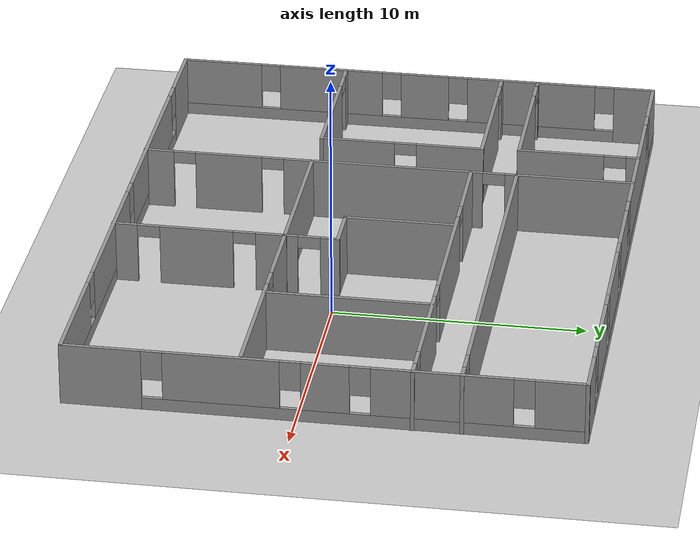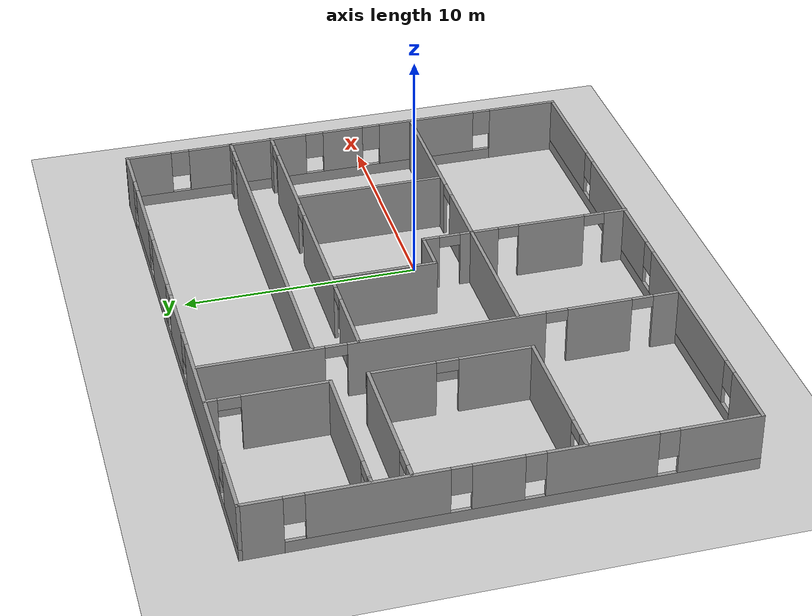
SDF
<?xml version="1.0"?>
<sdf version="1.6">
  <world name="default">

    <plugin
      filename="gz-sim-physics-system"
      name="gz::sim::systems::Physics">
    </plugin>
    <plugin
      filename="gz-sim-user-commands-system"
      name="gz::sim::systems::UserCommands">
    </plugin>
    <plugin
      filename="gz-sim-scene-broadcaster-system"
      name="gz::sim::systems::SceneBroadcaster">
    </plugin>
    <plugin
      filename="gz-sim-sensors-system"
      name="gz::sim::systems::Sensors">
      <render_engine>ogre2</render_engine>
    </plugin>
    <plugin
      filename="gz-sim-imu-system"
      name="gz::sim::systems::Imu">
    </plugin>
    <include>
      <uri>
        https://fuel.gazebosim.org/1.0/OpenRobotics/models/Ground Plane
      </uri>
    </include>

    <include>
      <uri>
        https://fuel.gazebosim.org/1.0/OpenRobotics/models/Sun
      </uri>
    </include>
    <gui fullscreen='0'>
      <camera name='user_camera'>
        <pose frame=''>0.319654 -0.235002 9.29441 0 1.5138 0.009599</pose>
        <view_controller>orbit</view_controller>
        <projection_type>perspective</projection_type>
      </camera>
      <plugin filename="MinimalScene" name="3D View">
        <gz-gui>
          <title>3D View</title>
          <property type="bool" key="showTitleBar">false</property>
          <property type="string" key="state">docked</property>
        </gz-gui>

        <engine>ogre2</engine>
        <scene>scene</scene>
        <ambient_light>0.4 0.4 0.4</ambient_light>
        <background_color>0.8 0.8 0.8</background_color>
        <camera_pose>0.319654 -0.235002 9.29441 0 1.5138 0.009599</camera_pose>
      </plugin>

      <plugin filename="EntityContextMenuPlugin" name="Entity context menu">
        <gz-gui>
          <property key="state" type="string">floating</property>
          <property key="width" type="double">5</property>
          <property key="height" type="double">5</property>
          <property key="showTitleBar" type="bool">false</property>
        </gz-gui>
      </plugin>
      <plugin filename="GzSceneManager" name="Scene Manager">
        <gz-gui>
          <property key="resizable" type="bool">false</property>
          <property key="width" type="double">5</property>
          <property key="height" type="double">5</property>
          <property key="state" type="string">floating</property>
          <property key="showTitleBar" type="bool">false</property>
        </gz-gui>
      </plugin>
      <plugin filename="InteractiveViewControl" name="Interactive view control">
        <gz-gui>
          <property key="resizable" type="bool">false</property>
          <property key="width" type="double">5</property>
          <property key="height" type="double">5</property>
          <property key="state" type="string">floating</property>
          <property key="showTitleBar" type="bool">false</property>
        </gz-gui>
      </plugin>
      <plugin filename="CameraTracking" name="Camera Tracking">
        <gz-gui>
          <property key="resizable" type="bool">false</property>
          <property key="width" type="double">5</property>
          <property key="height" type="double">5</property>
          <property key="state" type="string">floating</property>
          <property key="showTitleBar" type="bool">false</property>
        </gz-gui>
      </plugin>
      <plugin filename="MarkerManager" name="Marker manager">
        <gz-gui>
          <property key="resizable" type="bool">false</property>
          <property key="width" type="double">5</property>
          <property key="height" type="double">5</property>
          <property key="state" type="string">floating</property>
          <property key="showTitleBar" type="bool">false</property>
        </gz-gui>
      </plugin>
      <plugin filename="SelectEntities" name="Select Entities">
        <gz-gui>
          <property key="resizable" type="bool">false</property>
          <property key="width" type="double">5</property>
          <property key="height" type="double">5</property>
          <property key="state" type="string">floating</property>
          <property key="showTitleBar" type="bool">false</property>
        </gz-gui>
      </plugin>

      <plugin filename="Spawn" name="Spawn Entities">
        <gz-gui>
          <property key="resizable" type="bool">false</property>
          <property key="width" type="double">5</property>
          <property key="height" type="double">5</property>
          <property key="state" type="string">floating</property>
          <property key="showTitleBar" type="bool">false</property>
        </gz-gui>
      </plugin>

      <plugin filename="VisualizationCapabilities" name="Visualization Capabilities">
        <gz-gui>
          <property key="resizable" type="bool">false</property>
          <property key="width" type="double">5</property>
          <property key="height" type="double">5</property>
          <property key="state" type="string">floating</property>
          <property key="showTitleBar" type="bool">false</property>
        </gz-gui>
      </plugin>

      <!-- World control -->
      <plugin filename="WorldControl" name="World control">
        <gz-gui>
          <title>World control</title>
          <property type="bool" key="showTitleBar">false</property>
          <property type="bool" key="resizable">false</property>
          <property type="double" key="height">72</property>
          <property type="double" key="z">1</property>

          <property type="string" key="state">floating</property>
          <anchors target="3D View">
            <line own="left" target="left"/>
            <line own="bottom" target="bottom"/>
          </anchors>
        </gz-gui>

        <play_pause>true</play_pause>
        <step>true</step>
        <start_paused>true</start_paused>
        <use_event>true</use_event>

      </plugin>

      <!-- World statistics -->
      <plugin filename="WorldStats" name="World stats">
        <gz-gui>
          <title>World stats</title>
          <property type="bool" key="showTitleBar">false</property>
          <property type="bool" key="resizable">false</property>
          <property type="double" key="height">110</property>
          <property type="double" key="width">290</property>
          <property type="double" key="z">1</property>

          <property type="string" key="state">floating</property>
          <anchors target="3D View">
            <line own="right" target="right"/>
            <line own="bottom" target="bottom"/>
          </anchors>
        </gz-gui>

        <sim_time>true</sim_time>
        <real_time>true</real_time>
        <real_time_factor>true</real_time_factor>
        <iterations>true</iterations>
      </plugin>

      <!-- Insert simple shapes -->
      <plugin filename="Shapes" name="Shapes">
        <gz-gui>
          <property key="resizable" type="bool">false</property>
          <property key="x" type="double">0</property>
          <property key="y" type="double">0</property>
          <property key="width" type="double">250</property>
          <property key="height" type="double">50</property>
          <property key="state" type="string">floating</property>
          <property key="showTitleBar" type="bool">false</property>
          <property key="cardBackground" type="string">#666666</property>
        </gz-gui>
      </plugin>

      <!-- Insert lights -->
      <plugin filename="Lights" name="Lights">
        <gz-gui>
          <property key="resizable" type="bool">false</property>
          <property key="x" type="double">250</property>
          <property key="y" type="double">0</property>
          <property key="width" type="double">150</property>
          <property key="height" type="double">50</property>
          <property key="state" type="string">floating</property>
          <property key="showTitleBar" type="bool">false</property>
          <property key="cardBackground" type="string">#666666</property>
        </gz-gui>
      </plugin>

      <!-- Translate / rotate -->
      <plugin filename="TransformControl" name="Transform control">
        <gz-gui>
          <property key="resizable" type="bool">false</property>
          <property key="x" type="double">0</property>
          <property key="y" type="double">50</property>
          <property key="width" type="double">250</property>
          <property key="height" type="double">50</property>
          <property key="state" type="string">floating</property>
          <property key="showTitleBar" type="bool">false</property>
          <property key="cardBackground" type="string">#777777</property>
        </gz-gui>
      </plugin>

      <!-- Screenshot -->
      <plugin filename="Screenshot" name="Screenshot">
        <gz-gui>
          <property key="resizable" type="bool">false</property>
          <property key="x" type="double">250</property>
          <property key="y" type="double">50</property>
          <property key="width" type="double">50</property>
          <property key="height" type="double">50</property>
          <property key="state" type="string">floating</property>
          <property key="showTitleBar" type="bool">false</property>
          <property key="cardBackground" type="string">#777777</property>
        </gz-gui>
      </plugin>

      <!-- Copy/Paste -->
      <plugin filename="CopyPaste" name="CopyPaste">
        <gz-gui>
          <property key="resizable" type="bool">false</property>
          <property key="x" type="double">300</property>
          <property key="y" type="double">50</property>
          <property key="width" type="double">100</property>
          <property key="height" type="double">50</property>
          <property key="state" type="string">floating</property>
          <property key="showTitleBar" type="bool">false</property>
          <property key="cardBackground" type="string">#777777</property>
        </gz-gui>
      </plugin>

      <!-- Inspector -->
      <plugin filename="ComponentInspector" name="Component inspector">
        <gz-gui>
          <property type="bool" key="showTitleBar">false</property>
          <property type="string" key="state">docked</property>
        </gz-gui>
      </plugin>

      <!-- Entity tree -->
      <plugin filename="EntityTree" name="Entity tree">
        <gz-gui>
          <property type="bool" key="showTitleBar">false</property>
          <property type="string" key="state">docked</property>
        </gz-gui>
      </plugin>
    </gui>

    <physics type="ode">
      <real_time_update_rate>1000.0</real_time_update_rate>
      <max_step_size>0.001</max_step_size>
      <real_time_factor>1</real_time_factor>
      <ode>
        <solver>
          <type>quick</type>
          <iters>150</iters>
          <precon_iters>0</precon_iters>
          <sor>1.400000</sor>
          <use_dynamic_moi_rescaling>1</use_dynamic_moi_rescaling>
        </solver>
        <constraints>
          <cfm>0.00001</cfm>
          <erp>0.2</erp>
          <contact_max_correcting_vel>2000.000000</contact_max_correcting_vel>
          <contact_surface_layer>0.01000</contact_surface_layer>
        </constraints>
      </ode>
    </physics>

    <model name='RoomWorld'>
      <pose>-4 1 0 0 -0 0</pose>
      <link name='Wall_12'>
        <pose>-0.015924 -9.9164 0 0 -0 0</pose>
        <visual name='Wall_12_Visual_0'>
          <pose>-11.0832 0 1.25 0 -0 0</pose>
          <geometry>
            <box>
              <size>2.83352 0.15 2.5</size>
            </box>
          </geometry>
          <material>
            <script>
              <uri>file://media/materials/scripts/gazebo.material</uri>
              <name>Gazebo/Grey</name>
            </script>
            <ambient>1 1 1 1</ambient>
          </material>
        </visual>
        <collision name='Wall_12_Collision_0'>
          <geometry>
            <box>
              <size>2.83352 0.15 2.5</size>
            </box>
          </geometry>
          <pose>-11.0832 0 1.25 0 -0 0</pose>
          <max_contacts>10</max_contacts>
          <surface>
            <bounce/>
            <friction>
              <ode/>
            </friction>
            <contact>
              <ode/>
            </contact>
          </surface>
        </collision>
        <visual name='Wall_12_Visual_1'>
          <pose>1.41676 0 0.25 0 -0 0</pose>
          <geometry>
            <box>
              <size>22.1665 0.15 0.5</size>
            </box>
          </geometry>
          <material>
            <script>
              <uri>file://media/materials/scripts/gazebo.material</uri>
              <name>Gazebo/Grey</name>
            </script>
            <ambient>1 1 1 1</ambient>
          </material>
        </visual>
        <collision name='Wall_12_Collision_1'>
          <geometry>
            <box>
              <size>22.1665 0.15 0.5</size>
            </box>
          </geometry>
          <pose>1.41676 0 0.25 0 -0 0</pose>
          <max_contacts>10</max_contacts>
          <surface>
            <bounce/>
            <friction>
              <ode/>
            </friction>
            <contact>
              <ode/>
            </contact>
          </surface>
        </collision>
        <visual name='Wall_12_Visual_2'>
          <pose>-4.88323 0 1.5 0 -0 0</pose>
          <geometry>
            <box>
              <size>7.9665 0.15 2</size>
            </box>
          </geometry>
          <material>
            <script>
              <uri>file://media/materials/scripts/gazebo.material</uri>
              <name>Gazebo/Grey</name>
            </script>
            <ambient>1 1 1 1</ambient>
          </material>
        </visual>
        <collision name='Wall_12_Collision_2'>
          <geometry>
            <box>
              <size>7.9665 0.15 2</size>
            </box>
          </geometry>
          <pose>-4.88323 0 1.5 0 -0 0</pose>
          <max_contacts>10</max_contacts>
          <surface>
            <bounce/>
            <friction>
              <ode/>
            </friction>
            <contact>
              <ode/>
            </contact>
          </surface>
        </collision>
        <visual name='Wall_12_Visual_3'>
          <pose>3.30501 0 1.5 0 -0 0</pose>
          <geometry>
            <box>
              <size>6.80997 0.15 2</size>
            </box>
          </geometry>
          <material>
            <script>
              <uri>file://media/materials/scripts/gazebo.material</uri>
              <name>Gazebo/Grey</name>
            </script>
            <ambient>1 1 1 1</ambient>
          </material>
        </visual>
        <collision name='Wall_12_Collision_3'>
          <geometry>
            <box>
              <size>6.80997 0.15 2</size>
            </box>
          </geometry>
          <pose>3.30501 0 1.5 0 -0 0</pose>
          <max_contacts>10</max_contacts>
          <surface>
            <bounce/>
            <friction>
              <ode/>
            </friction>
            <contact>
              <ode/>
            </contact>
          </surface>
        </collision>
        <visual name='Wall_12_Visual_4'>
          <pose>10.005 0 1.5 0 -0 0</pose>
          <geometry>
            <box>
              <size>4.99001 0.15 2</size>
            </box>
          </geometry>
          <material>
            <script>
              <uri>file://media/materials/scripts/gazebo.material</uri>
              <name>Gazebo/Grey</name>
            </script>
            <ambient>1 1 1 1</ambient>
          </material>
        </visual>
        <collision name='Wall_12_Collision_4'>
          <geometry>
            <box>
              <size>4.99001 0.15 2</size>
            </box>
          </geometry>
          <pose>10.005 0 1.5 0 -0 0</pose>
          <max_contacts>10</max_contacts>
          <surface>
            <bounce/>
            <friction>
              <ode/>
            </friction>
            <contact>
              <ode/>
            </contact>
          </surface>
        </collision>
        <visual name='Wall_12_Visual_5'>
          <pose>-9.26648 0 1.9 0 -0 0</pose>
          <geometry>
            <box>
              <size>0.8 0.15 1.2</size>
            </box>
          </geometry>
          <material>
            <script>
              <uri>file://media/materials/scripts/gazebo.material</uri>
              <name>Gazebo/Grey</name>
            </script>
            <ambient>1 1 1 1</ambient>
          </material>
        </visual>
        <collision name='Wall_12_Collision_5'>
          <geometry>
            <box>
              <size>0.8 0.15 1.2</size>
            </box>
          </geometry>
          <pose>-9.26648 0 1.9 0 -0 0</pose>
          <max_contacts>10</max_contacts>
          <surface>
            <bounce/>
            <friction>
              <ode/>
            </friction>
            <contact>
              <ode/>
            </contact>
          </surface>
        </collision>
        <visual name='Wall_12_Visual_6'>
          <pose>-0.499978 0 1.9 0 -0 0</pose>
          <geometry>
            <box>
              <size>0.8 0.15 1.2</size>
            </box>
          </geometry>
          <material>
            <script>
              <uri>file://media/materials/scripts/gazebo.material</uri>
              <name>Gazebo/Grey</name>
            </script>
            <ambient>1 1 1 1</ambient>
          </material>
        </visual>
        <collision name='Wall_12_Collision_6'>
          <geometry>
            <box>
              <size>0.8 0.15 1.2</size>
            </box>
          </geometry>
          <pose>-0.499978 0 1.9 0 -0 0</pose>
          <max_contacts>10</max_contacts>
          <surface>
            <bounce/>
            <friction>
              <ode/>
            </friction>
            <contact>
              <ode/>
            </contact>
          </surface>
        </collision>
        <visual name='Wall_12_Visual_7'>
          <pose>7.10999 0 1.9 0 -0 0</pose>
          <geometry>
            <box>
              <size>0.8 0.15 1.2</size>
            </box>
          </geometry>
          <material>
            <script>
              <uri>file://media/materials/scripts/gazebo.material</uri>
              <name>Gazebo/Grey</name>
            </script>
            <ambient>1 1 1 1</ambient>
          </material>
        </visual>
        <collision name='Wall_12_Collision_7'>
          <geometry>
            <box>
              <size>0.8 0.15 1.2</size>
            </box>
          </geometry>
          <pose>7.10999 0 1.9 0 -0 0</pose>
          <max_contacts>10</max_contacts>
          <surface>
            <bounce/>
            <friction>
              <ode/>
            </friction>
            <contact>
              <ode/>
            </contact>
          </surface>
        </collision>
        <velocity_decay>
          <linear>0</linear>
          <angular>0</angular>
        </velocity_decay>
        <self_collide>0</self_collide>
        <kinematic>0</kinematic>
        <gravity>1</gravity>
      </link>
      <link name='Wall_13'>
        <pose>12.4091 0.008604 0 0 -0 1.5708</pose>
        <visual name='Wall_13_Visual_0'>
          <pose>-8.43232 0 1.25 0 -0 0</pose>
          <geometry>
            <box>
              <size>3.13536 0.15 2.5</size>
            </box>
          </geometry>
          <material>
            <script>
              <uri>file://media/materials/scripts/gazebo.material</uri>
              <name>Gazebo/Grey</name>
            </script>
            <ambient>1 1 1 1</ambient>
          </material>
        </visual>
        <collision name='Wall_13_Collision_0'>
          <geometry>
            <box>
              <size>3.13536 0.15 2.5</size>
            </box>
          </geometry>
          <pose>-8.43232 0 1.25 0 -0 0</pose>
          <max_contacts>10</max_contacts>
          <surface>
            <bounce/>
            <friction>
              <ode/>
            </friction>
            <contact>
              <ode/>
            </contact>
          </surface>
        </collision>
        <visual name='Wall_13_Visual_1'>
          <pose>1.56768 0 0.25 0 -0 0</pose>
          <geometry>
            <box>
              <size>16.8646 0.15 0.5</size>
            </box>
          </geometry>
          <material>
            <script>
              <uri>file://media/materials/scripts/gazebo.material</uri>
              <name>Gazebo/Grey</name>
            </script>
            <ambient>1 1 1 1</ambient>
          </material>
        </visual>
        <collision name='Wall_13_Collision_1'>
          <geometry>
            <box>
              <size>16.8646 0.15 0.5</size>
            </box>
          </geometry>
          <pose>1.56768 0 0.25 0 -0 0</pose>
          <max_contacts>10</max_contacts>
          <surface>
            <bounce/>
            <friction>
              <ode/>
            </friction>
            <contact>
              <ode/>
            </contact>
          </surface>
        </collision>
        <visual name='Wall_13_Visual_2'>
          <pose>-3.83932 0 1.5 0 -0 0</pose>
          <geometry>
            <box>
              <size>4.45065 0.15 2</size>
            </box>
          </geometry>
          <material>
            <script>
              <uri>file://media/materials/scripts/gazebo.material</uri>
              <name>Gazebo/Grey</name>
            </script>
            <ambient>1 1 1 1</ambient>
          </material>
        </visual>
        <collision name='Wall_13_Collision_2'>
          <geometry>
            <box>
              <size>4.45065 0.15 2</size>
            </box>
          </geometry>
          <pose>-3.83932 0 1.5 0 -0 0</pose>
          <max_contacts>10</max_contacts>
          <surface>
            <bounce/>
            <friction>
              <ode/>
            </friction>
            <contact>
              <ode/>
            </contact>
          </surface>
        </collision>
        <visual name='Wall_13_Visual_3'>
          <pose>0.104448 0 1.5 0 -0 0</pose>
          <geometry>
            <box>
              <size>1.83689 0.15 2</size>
            </box>
          </geometry>
          <material>
            <script>
              <uri>file://media/materials/scripts/gazebo.material</uri>
              <name>Gazebo/Grey</name>
            </script>
            <ambient>1 1 1 1</ambient>
          </material>
        </visual>
        <collision name='Wall_13_Collision_3'>
          <geometry>
            <box>
              <size>1.83689 0.15 2</size>
            </box>
          </geometry>
          <pose>0.104448 0 1.5 0 -0 0</pose>
          <max_contacts>10</max_contacts>
          <surface>
            <bounce/>
            <friction>
              <ode/>
            </friction>
            <contact>
              <ode/>
            </contact>
          </surface>
        </collision>
        <visual name='Wall_13_Visual_4'>
          <pose>4.49926 0 1.5 0 -0 0</pose>
          <geometry>
            <box>
              <size>5.35274 0.15 2</size>
            </box>
          </geometry>
          <material>
            <script>
              <uri>file://media/materials/scripts/gazebo.material</uri>
              <name>Gazebo/Grey</name>
            </script>
            <ambient>1 1 1 1</ambient>
          </material>
        </visual>
        <collision name='Wall_13_Collision_4'>
          <geometry>
            <box>
              <size>5.35274 0.15 2</size>
            </box>
          </geometry>
          <pose>4.49926 0 1.5 0 -0 0</pose>
          <max_contacts>10</max_contacts>
          <surface>
            <bounce/>
            <friction>
              <ode/>
            </friction>
            <contact>
              <ode/>
            </contact>
          </surface>
        </collision>
        <visual name='Wall_13_Visual_5'>
          <pose>8.98782 0 1.5 0 -0 0</pose>
          <geometry>
            <box>
              <size>2.02437 0.15 2</size>
            </box>
          </geometry>
          <material>
            <script>
              <uri>file://media/materials/scripts/gazebo.material</uri>
              <name>Gazebo/Grey</name>
            </script>
            <ambient>1 1 1 1</ambient>
          </material>
        </visual>
        <collision name='Wall_13_Collision_5'>
          <geometry>
            <box>
              <size>2.02437 0.15 2</size>
            </box>
          </geometry>
          <pose>8.98782 0 1.5 0 -0 0</pose>
          <max_contacts>10</max_contacts>
          <surface>
            <bounce/>
            <friction>
              <ode/>
            </friction>
            <contact>
              <ode/>
            </contact>
          </surface>
        </collision>
        <visual name='Wall_13_Visual_6'>
          <pose>-6.46464 0 1.9 0 -0 0</pose>
          <geometry>
            <box>
              <size>0.8 0.15 1.2</size>
            </box>
          </geometry>
          <material>
            <script>
              <uri>file://media/materials/scripts/gazebo.material</uri>
              <name>Gazebo/Grey</name>
            </script>
            <ambient>1 1 1 1</ambient>
          </material>
        </visual>
        <collision name='Wall_13_Collision_6'>
          <geometry>
            <box>
              <size>0.8 0.15 1.2</size>
            </box>
          </geometry>
          <pose>-6.46464 0 1.9 0 -0 0</pose>
          <max_contacts>10</max_contacts>
          <surface>
            <bounce/>
            <friction>
              <ode/>
            </friction>
            <contact>
              <ode/>
            </contact>
          </surface>
        </collision>
        <visual name='Wall_13_Visual_7'>
          <pose>-1.214 0 1.9 0 -0 0</pose>
          <geometry>
            <box>
              <size>0.8 0.15 1.2</size>
            </box>
          </geometry>
          <material>
            <script>
              <uri>file://media/materials/scripts/gazebo.material</uri>
              <name>Gazebo/Grey</name>
            </script>
            <ambient>1 1 1 1</ambient>
          </material>
        </visual>
        <collision name='Wall_13_Collision_7'>
          <geometry>
            <box>
              <size>0.8 0.15 1.2</size>
            </box>
          </geometry>
          <pose>-1.214 0 1.9 0 -0 0</pose>
          <max_contacts>10</max_contacts>
          <surface>
            <bounce/>
            <friction>
              <ode/>
            </friction>
            <contact>
              <ode/>
            </contact>
          </surface>
        </collision>
        <visual name='Wall_13_Visual_8'>
          <pose>1.42289 0 1.9 0 -0 0</pose>
          <geometry>
            <box>
              <size>0.8 0.15 1.2</size>
            </box>
          </geometry>
          <material>
            <script>
              <uri>file://media/materials/scripts/gazebo.material</uri>
              <name>Gazebo/Grey</name>
            </script>
            <ambient>1 1 1 1</ambient>
          </material>
        </visual>
        <collision name='Wall_13_Collision_8'>
          <geometry>
            <box>
              <size>0.8 0.15 1.2</size>
            </box>
          </geometry>
          <pose>1.42289 0 1.9 0 -0 0</pose>
          <max_contacts>10</max_contacts>
          <surface>
            <bounce/>
            <friction>
              <ode/>
            </friction>
            <contact>
              <ode/>
            </contact>
          </surface>
        </collision>
        <visual name='Wall_13_Visual_9'>
          <pose>7.57563 0 1.9 0 -0 0</pose>
          <geometry>
            <box>
              <size>0.8 0.15 1.2</size>
            </box>
          </geometry>
          <material>
            <script>
              <uri>file://media/materials/scripts/gazebo.material</uri>
              <name>Gazebo/Grey</name>
            </script>
            <ambient>1 1 1 1</ambient>
          </material>
        </visual>
        <collision name='Wall_13_Collision_9'>
          <geometry>
            <box>
              <size>0.8 0.15 1.2</size>
            </box>
          </geometry>
          <pose>7.57563 0 1.9 0 -0 0</pose>
          <max_contacts>10</max_contacts>
          <surface>
            <bounce/>
            <friction>
              <ode/>
            </friction>
            <contact>
              <ode/>
            </contact>
          </surface>
        </collision>
        <velocity_decay>
          <linear>0</linear>
          <angular>0</angular>
        </velocity_decay>
        <self_collide>0</self_collide>
        <kinematic>0</kinematic>
        <gravity>1</gravity>
      </link>
      <link name='Wall_14'>
        <pose>-0.015924 9.9336 0 0 -0 3.14159</pose>
        <visual name='Wall_14_Visual_0'>
          <pose>-11.4391 0 1.25 0 -0 0</pose>
          <geometry>
            <box>
              <size>2.12181 0.15 2.5</size>
            </box>
          </geometry>
          <material>
            <script>
              <uri>file://media/materials/scripts/gazebo.material</uri>
              <name>Gazebo/Grey</name>
            </script>
            <ambient>1 1 1 1</ambient>
          </material>
        </visual>
        <collision name='Wall_14_Collision_0'>
          <geometry>
            <box>
              <size>2.12181 0.15 2.5</size>
            </box>
          </geometry>
          <pose>-11.4391 0 1.25 0 -0 0</pose>
          <max_contacts>10</max_contacts>
          <surface>
            <bounce/>
            <friction>
              <ode/>
            </friction>
            <contact>
              <ode/>
            </contact>
          </surface>
        </collision>
        <visual name='Wall_14_Visual_1'>
          <pose>1.06091 0 0.25 0 -0 0</pose>
          <geometry>
            <box>
              <size>22.8782 0.15 0.5</size>
            </box>
          </geometry>
          <material>
            <script>
              <uri>file://media/materials/scripts/gazebo.material</uri>
              <name>Gazebo/Grey</name>
            </script>
            <ambient>1 1 1 1</ambient>
          </material>
        </visual>
        <collision name='Wall_14_Collision_1'>
          <geometry>
            <box>
              <size>22.8782 0.15 0.5</size>
            </box>
          </geometry>
          <pose>1.06091 0 0.25 0 -0 0</pose>
          <max_contacts>10</max_contacts>
          <surface>
            <bounce/>
            <friction>
              <ode/>
            </friction>
            <contact>
              <ode/>
            </contact>
          </surface>
        </collision>
        <visual name='Wall_14_Visual_2'>
          <pose>-7.93113 0 1.5 0 -0 0</pose>
          <geometry>
            <box>
              <size>3.29412 0.15 2</size>
            </box>
          </geometry>
          <material>
            <script>
              <uri>file://media/materials/scripts/gazebo.material</uri>
              <name>Gazebo/Grey</name>
            </script>
            <ambient>1 1 1 1</ambient>
          </material>
        </visual>
        <collision name='Wall_14_Collision_2'>
          <geometry>
            <box>
              <size>3.29412 0.15 2</size>
            </box>
          </geometry>
          <pose>-7.93113 0 1.5 0 -0 0</pose>
          <max_contacts>10</max_contacts>
          <surface>
            <bounce/>
            <friction>
              <ode/>
            </friction>
            <contact>
              <ode/>
            </contact>
          </surface>
        </collision>
        <visual name='Wall_14_Visual_3'>
          <pose>-3.75605 0 1.5 0 -0 0</pose>
          <geometry>
            <box>
              <size>3.45603 0.15 2</size>
            </box>
          </geometry>
          <material>
            <script>
              <uri>file://media/materials/scripts/gazebo.material</uri>
              <name>Gazebo/Grey</name>
            </script>
            <ambient>1 1 1 1</ambient>
          </material>
        </visual>
        <collision name='Wall_14_Collision_3'>
          <geometry>
            <box>
              <size>3.45603 0.15 2</size>
            </box>
          </geometry>
          <pose>-3.75605 0 1.5 0 -0 0</pose>
          <max_contacts>10</max_contacts>
          <surface>
            <bounce/>
            <friction>
              <ode/>
            </friction>
            <contact>
              <ode/>
            </contact>
          </surface>
        </collision>
        <visual name='Wall_14_Visual_4'>
          <pose>0.141454 0 1.5 0 -0 0</pose>
          <geometry>
            <box>
              <size>2.73898 0.15 2</size>
            </box>
          </geometry>
          <material>
            <script>
              <uri>file://media/materials/scripts/gazebo.material</uri>
              <name>Gazebo/Grey</name>
            </script>
            <ambient>1 1 1 1</ambient>
          </material>
        </visual>
        <collision name='Wall_14_Collision_4'>
          <geometry>
            <box>
              <size>2.73898 0.15 2</size>
            </box>
          </geometry>
          <pose>0.141454 0 1.5 0 -0 0</pose>
          <max_contacts>10</max_contacts>
          <surface>
            <bounce/>
            <friction>
              <ode/>
            </friction>
            <contact>
              <ode/>
            </contact>
          </surface>
        </collision>
        <visual name='Wall_14_Visual_5'>
          <pose>5.73906 0 1.5 0 -0 0</pose>
          <geometry>
            <box>
              <size>6.85623 0.15 2</size>
            </box>
          </geometry>
          <material>
            <script>
              <uri>file://media/materials/scripts/gazebo.material</uri>
              <name>Gazebo/Grey</name>
            </script>
            <ambient>1 1 1 1</ambient>
          </material>
        </visual>
        <collision name='Wall_14_Collision_5'>
          <geometry>
            <box>
              <size>6.85623 0.15 2</size>
            </box>
          </geometry>
          <pose>5.73906 0 1.5 0 -0 0</pose>
          <max_contacts>10</max_contacts>
          <surface>
            <bounce/>
            <friction>
              <ode/>
            </friction>
            <contact>
              <ode/>
            </contact>
          </surface>
        </collision>
        <visual name='Wall_14_Visual_6'>
          <pose>11.2336 0 1.5 0 -0 0</pose>
          <geometry>
            <box>
              <size>2.53282 0.15 2</size>
            </box>
          </geometry>
          <material>
            <script>
              <uri>file://media/materials/scripts/gazebo.material</uri>
              <name>Gazebo/Grey</name>
            </script>
            <ambient>1 1 1 1</ambient>
          </material>
        </visual>
        <collision name='Wall_14_Collision_6'>
          <geometry>
            <box>
              <size>2.53282 0.15 2</size>
            </box>
          </geometry>
          <pose>11.2336 0 1.5 0 -0 0</pose>
          <max_contacts>10</max_contacts>
          <surface>
            <bounce/>
            <friction>
              <ode/>
            </friction>
            <contact>
              <ode/>
            </contact>
          </surface>
        </collision>
        <visual name='Wall_14_Visual_7'>
          <pose>-9.97819 0 1.9 0 -0 0</pose>
          <geometry>
            <box>
              <size>0.8 0.15 1.2</size>
            </box>
          </geometry>
          <material>
            <script>
              <uri>file://media/materials/scripts/gazebo.material</uri>
              <name>Gazebo/Grey</name>
            </script>
            <ambient>1 1 1 1</ambient>
          </material>
        </visual>
        <collision name='Wall_14_Collision_7'>
          <geometry>
            <box>
              <size>0.8 0.15 1.2</size>
            </box>
          </geometry>
          <pose>-9.97819 0 1.9 0 -0 0</pose>
          <max_contacts>10</max_contacts>
          <surface>
            <bounce/>
            <friction>
              <ode/>
            </friction>
            <contact>
              <ode/>
            </contact>
          </surface>
        </collision>
        <visual name='Wall_14_Visual_8'>
          <pose>-5.88407 0 1.9 0 -0 0</pose>
          <geometry>
            <box>
              <size>0.8 0.15 1.2</size>
            </box>
          </geometry>
          <material>
            <script>
              <uri>file://media/materials/scripts/gazebo.material</uri>
              <name>Gazebo/Grey</name>
            </script>
            <ambient>1 1 1 1</ambient>
          </material>
        </visual>
        <collision name='Wall_14_Collision_8'>
          <geometry>
            <box>
              <size>0.8 0.15 1.2</size>
            </box>
          </geometry>
          <pose>-5.88407 0 1.9 0 -0 0</pose>
          <max_contacts>10</max_contacts>
          <surface>
            <bounce/>
            <friction>
              <ode/>
            </friction>
            <contact>
              <ode/>
            </contact>
          </surface>
        </collision>
        <visual name='Wall_14_Visual_9'>
          <pose>-1.62804 0 1.9 0 -0 0</pose>
          <geometry>
            <box>
              <size>0.8 0.15 1.2</size>
            </box>
          </geometry>
          <material>
            <script>
              <uri>file://media/materials/scripts/gazebo.material</uri>
              <name>Gazebo/Grey</name>
            </script>
            <ambient>1 1 1 1</ambient>
          </material>
        </visual>
        <collision name='Wall_14_Collision_9'>
          <geometry>
            <box>
              <size>0.8 0.15 1.2</size>
            </box>
          </geometry>
          <pose>-1.62804 0 1.9 0 -0 0</pose>
          <max_contacts>10</max_contacts>
          <surface>
            <bounce/>
            <friction>
              <ode/>
            </friction>
            <contact>
              <ode/>
            </contact>
          </surface>
        </collision>
        <visual name='Wall_14_Visual_10'>
          <pose>1.91094 0 1.9 0 -0 0</pose>
          <geometry>
            <box>
              <size>0.8 0.15 1.2</size>
            </box>
          </geometry>
          <material>
            <script>
              <uri>file://media/materials/scripts/gazebo.material</uri>
              <name>Gazebo/Grey</name>
            </script>
            <ambient>1 1 1 1</ambient>
          </material>
        </visual>
        <collision name='Wall_14_Collision_10'>
          <geometry>
            <box>
              <size>0.8 0.15 1.2</size>
            </box>
          </geometry>
          <pose>1.91094 0 1.9 0 -0 0</pose>
          <max_contacts>10</max_contacts>
          <surface>
            <bounce/>
            <friction>
              <ode/>
            </friction>
            <contact>
              <ode/>
            </contact>
          </surface>
        </collision>
        <visual name='Wall_14_Visual_11'>
          <pose>9.56718 0 1.9 0 -0 0</pose>
          <geometry>
            <box>
              <size>0.8 0.15 1.2</size>
            </box>
          </geometry>
          <material>
            <script>
              <uri>file://media/materials/scripts/gazebo.material</uri>
              <name>Gazebo/Grey</name>
            </script>
            <ambient>1 1 1 1</ambient>
          </material>
        </visual>
        <collision name='Wall_14_Collision_11'>
          <geometry>
            <box>
              <size>0.8 0.15 1.2</size>
            </box>
          </geometry>
          <pose>9.56718 0 1.9 0 -0 0</pose>
          <max_contacts>10</max_contacts>
          <surface>
            <bounce/>
            <friction>
              <ode/>
            </friction>
            <contact>
              <ode/>
            </contact>
          </surface>
        </collision>
        <velocity_decay>
          <linear>0</linear>
          <angular>0</angular>
        </velocity_decay>
        <self_collide>0</self_collide>
        <kinematic>0</kinematic>
        <gravity>1</gravity>
      </link>
      <link name='Wall_15'>
        <pose>-12.4409 0.008604 0 0 0 -1.5708</pose>
        <visual name='Wall_15_Visual_0'>
          <pose>-9.14973 0 1.25 0 -0 0</pose>
          <geometry>
            <box>
              <size>1.70054 0.15 2.5</size>
            </box>
          </geometry>
          <material>
            <script>
              <uri>file://media/materials/scripts/gazebo.material</uri>
              <name>Gazebo/Grey</name>
            </script>
            <ambient>1 1 1 1</ambient>
          </material>
        </visual>
        <collision name='Wall_15_Collision_0'>
          <geometry>
            <box>
              <size>1.70054 0.15 2.5</size>
            </box>
          </geometry>
          <pose>-9.14973 0 1.25 0 -0 0</pose>
          <max_contacts>10</max_contacts>
          <surface>
            <bounce/>
            <friction>
              <ode/>
            </friction>
            <contact>
              <ode/>
            </contact>
          </surface>
        </collision>
        <visual name='Wall_15_Visual_1'>
          <pose>0.850269 0 0.25 0 -0 0</pose>
          <geometry>
            <box>
              <size>18.2995 0.15 0.5</size>
            </box>
          </geometry>
          <material>
            <script>
              <uri>file://media/materials/scripts/gazebo.material</uri>
              <name>Gazebo/Grey</name>
            </script>
            <ambient>1 1 1 1</ambient>
          </material>
        </visual>
        <collision name='Wall_15_Collision_1'>
          <geometry>
            <box>
              <size>18.2995 0.15 0.5</size>
            </box>
          </geometry>
          <pose>0.850269 0 0.25 0 -0 0</pose>
          <max_contacts>10</max_contacts>
          <surface>
            <bounce/>
            <friction>
              <ode/>
            </friction>
            <contact>
              <ode/>
            </contact>
          </surface>
        </collision>
        <visual name='Wall_15_Visual_2'>
          <pose>-4.81153 0 1.5 0 -0 0</pose>
          <geometry>
            <box>
              <size>5.37587 0.15 2</size>
            </box>
          </geometry>
          <material>
            <script>
              <uri>file://media/materials/scripts/gazebo.material</uri>
              <name>Gazebo/Grey</name>
            </script>
            <ambient>1 1 1 1</ambient>
          </material>
        </visual>
        <collision name='Wall_15_Collision_2'>
          <geometry>
            <box>
              <size>5.37587 0.15 2</size>
            </box>
          </geometry>
          <pose>-4.81153 0 1.5 0 -0 0</pose>
          <max_contacts>10</max_contacts>
          <surface>
            <bounce/>
            <friction>
              <ode/>
            </friction>
            <contact>
              <ode/>
            </contact>
          </surface>
        </collision>
        <visual name='Wall_15_Visual_3'>
          <pose>-0.312623 0 1.5 0 -0 0</pose>
          <geometry>
            <box>
              <size>2.02193 0.15 2</size>
            </box>
          </geometry>
          <material>
            <script>
              <uri>file://media/materials/scripts/gazebo.material</uri>
              <name>Gazebo/Grey</name>
            </script>
            <ambient>1 1 1 1</ambient>
          </material>
        </visual>
        <collision name='Wall_15_Collision_3'>
          <geometry>
            <box>
              <size>2.02193 0.15 2</size>
            </box>
          </geometry>
          <pose>-0.312623 0 1.5 0 -0 0</pose>
          <max_contacts>10</max_contacts>
          <surface>
            <bounce/>
            <friction>
              <ode/>
            </friction>
            <contact>
              <ode/>
            </contact>
          </surface>
        </collision>
        <visual name='Wall_15_Visual_4'>
          <pose>3.67741 0 1.5 0 -0 0</pose>
          <geometry>
            <box>
              <size>4.35813 0.15 2</size>
            </box>
          </geometry>
          <material>
            <script>
              <uri>file://media/materials/scripts/gazebo.material</uri>
              <name>Gazebo/Grey</name>
            </script>
            <ambient>1 1 1 1</ambient>
          </material>
        </visual>
        <collision name='Wall_15_Collision_4'>
          <geometry>
            <box>
              <size>4.35813 0.15 2</size>
            </box>
          </geometry>
          <pose>3.67741 0 1.5 0 -0 0</pose>
          <max_contacts>10</max_contacts>
          <surface>
            <bounce/>
            <friction>
              <ode/>
            </friction>
            <contact>
              <ode/>
            </contact>
          </surface>
        </collision>
        <visual name='Wall_15_Visual_5'>
          <pose>8.32823 0 1.5 0 -0 0</pose>
          <geometry>
            <box>
              <size>3.34353 0.15 2</size>
            </box>
          </geometry>
          <material>
            <script>
              <uri>file://media/materials/scripts/gazebo.material</uri>
              <name>Gazebo/Grey</name>
            </script>
            <ambient>1 1 1 1</ambient>
          </material>
        </visual>
        <collision name='Wall_15_Collision_5'>
          <geometry>
            <box>
              <size>3.34353 0.15 2</size>
            </box>
          </geometry>
          <pose>8.32823 0 1.5 0 -0 0</pose>
          <max_contacts>10</max_contacts>
          <surface>
            <bounce/>
            <friction>
              <ode/>
            </friction>
            <contact>
              <ode/>
            </contact>
          </surface>
        </collision>
        <visual name='Wall_15_Visual_6'>
          <pose>-7.89946 0 1.9 0 -0 0</pose>
          <geometry>
            <box>
              <size>0.8 0.15 1.2</size>
            </box>
          </geometry>
          <material>
            <script>
              <uri>file://media/materials/scripts/gazebo.material</uri>
              <name>Gazebo/Grey</name>
            </script>
            <ambient>1 1 1 1</ambient>
          </material>
        </visual>
        <collision name='Wall_15_Collision_6'>
          <geometry>
            <box>
              <size>0.8 0.15 1.2</size>
            </box>
          </geometry>
          <pose>-7.89946 0 1.9 0 -0 0</pose>
          <max_contacts>10</max_contacts>
          <surface>
            <bounce/>
            <friction>
              <ode/>
            </friction>
            <contact>
              <ode/>
            </contact>
          </surface>
        </collision>
        <visual name='Wall_15_Visual_7'>
          <pose>-1.72359 0 1.9 0 -0 0</pose>
          <geometry>
            <box>
              <size>0.8 0.15 1.2</size>
            </box>
          </geometry>
          <material>
            <script>
              <uri>file://media/materials/scripts/gazebo.material</uri>
              <name>Gazebo/Grey</name>
            </script>
            <ambient>1 1 1 1</ambient>
          </material>
        </visual>
        <collision name='Wall_15_Collision_7'>
          <geometry>
            <box>
              <size>0.8 0.15 1.2</size>
            </box>
          </geometry>
          <pose>-1.72359 0 1.9 0 -0 0</pose>
          <max_contacts>10</max_contacts>
          <surface>
            <bounce/>
            <friction>
              <ode/>
            </friction>
            <contact>
              <ode/>
            </contact>
          </surface>
        </collision>
        <visual name='Wall_15_Visual_8'>
          <pose>1.09834 0 1.9 0 -0 0</pose>
          <geometry>
            <box>
              <size>0.8 0.15 1.2</size>
            </box>
          </geometry>
          <material>
            <script>
              <uri>file://media/materials/scripts/gazebo.material</uri>
              <name>Gazebo/Grey</name>
            </script>
            <ambient>1 1 1 1</ambient>
          </material>
        </visual>
        <collision name='Wall_15_Collision_8'>
          <geometry>
            <box>
              <size>0.8 0.15 1.2</size>
            </box>
          </geometry>
          <pose>1.09834 0 1.9 0 -0 0</pose>
          <max_contacts>10</max_contacts>
          <surface>
            <bounce/>
            <friction>
              <ode/>
            </friction>
            <contact>
              <ode/>
            </contact>
          </surface>
        </collision>
        <visual name='Wall_15_Visual_9'>
          <pose>6.25647 0 1.9 0 -0 0</pose>
          <geometry>
            <box>
              <size>0.8 0.15 1.2</size>
            </box>
          </geometry>
          <material>
            <script>
              <uri>file://media/materials/scripts/gazebo.material</uri>
              <name>Gazebo/Grey</name>
            </script>
            <ambient>1 1 1 1</ambient>
          </material>
        </visual>
        <collision name='Wall_15_Collision_9'>
          <geometry>
            <box>
              <size>0.8 0.15 1.2</size>
            </box>
          </geometry>
          <pose>6.25647 0 1.9 0 -0 0</pose>
          <max_contacts>10</max_contacts>
          <surface>
            <bounce/>
            <friction>
              <ode/>
            </friction>
            <contact>
              <ode/>
            </contact>
          </surface>
        </collision>
        <velocity_decay>
          <linear>0</linear>
          <angular>0</angular>
        </velocity_decay>
        <self_collide>0</self_collide>
        <kinematic>0</kinematic>
        <gravity>1</gravity>
      </link>
      <link name='Wall_17'>
        <pose>-9.20541 3.56611 0 0 -0 0</pose>
        <visual name='Wall_17_Visual_0'>
          <pose>-2.94296 0 1.25 0 -0 0</pose>
          <geometry>
            <box>
              <size>0.614084 0.15 2.5</size>
            </box>
          </geometry>
          <material>
            <script>
              <uri>file://media/materials/scripts/gazebo.material</uri>
              <name>Gazebo/Grey</name>
            </script>
            <ambient>1 1 1 1</ambient>
          </material>
        </visual>
        <collision name='Wall_17_Collision_0'>
          <geometry>
            <box>
              <size>0.614084 0.15 2.5</size>
            </box>
          </geometry>
          <pose>-2.94296 0 1.25 0 -0 0</pose>
          <max_contacts>10</max_contacts>
          <surface>
            <bounce/>
            <friction>
              <ode/>
            </friction>
            <contact>
              <ode/>
            </contact>
          </surface>
        </collision>
        <visual name='Wall_17_Visual_1'>
          <pose>0.757042 0 1.25 0 -0 0</pose>
          <geometry>
            <box>
              <size>4.98592 0.15 2.5</size>
            </box>
          </geometry>
          <material>
            <script>
              <uri>file://media/materials/scripts/gazebo.material</uri>
              <name>Gazebo/Grey</name>
            </script>
            <ambient>1 1 1 1</ambient>
          </material>
        </visual>
        <collision name='Wall_17_Collision_1'>
          <geometry>
            <box>
              <size>4.98592 0.15 2.5</size>
            </box>
          </geometry>
          <pose>0.757042 0 1.25 0 -0 0</pose>
          <max_contacts>10</max_contacts>
          <surface>
            <bounce/>
            <friction>
              <ode/>
            </friction>
            <contact>
              <ode/>
            </contact>
          </surface>
        </collision>
        <visual name='Wall_17_Visual_2'>
          <pose>-2.18592 0 2.25 0 -0 0</pose>
          <geometry>
            <box>
              <size>0.9 0.15 0.5</size>
            </box>
          </geometry>
          <material>
            <script>
              <uri>file://media/materials/scripts/gazebo.material</uri>
              <name>Gazebo/Grey</name>
            </script>
            <ambient>1 1 1 1</ambient>
          </material>
        </visual>
        <collision name='Wall_17_Collision_2'>
          <geometry>
            <box>
              <size>0.9 0.15 0.5</size>
            </box>
          </geometry>
          <pose>-2.18592 0 2.25 0 -0 0</pose>
          <max_contacts>10</max_contacts>
          <surface>
            <bounce/>
            <friction>
              <ode/>
            </friction>
            <contact>
              <ode/>
            </contact>
          </surface>
        </collision>
        <velocity_decay>
          <linear>0</linear>
          <angular>0</angular>
        </velocity_decay>
        <self_collide>0</self_collide>
        <kinematic>0</kinematic>
        <gravity>1</gravity>
      </link>
      <link name='Wall_18'>
        <pose>-6.03041 0.266112 0 0 0 -1.5708</pose>
        <visual name='Wall_18_Visual_0'>
          <pose>-1.99435 0 1.25 0 -0 0</pose>
          <geometry>
            <box>
              <size>2.7613 0.15 2.5</size>
            </box>
          </geometry>
          <material>
            <script>
              <uri>file://media/materials/scripts/gazebo.material</uri>
              <name>Gazebo/Grey</name>
            </script>
            <ambient>1 1 1 1</ambient>
          </material>
        </visual>
        <collision name='Wall_18_Collision_0'>
          <geometry>
            <box>
              <size>2.7613 0.15 2.5</size>
            </box>
          </geometry>
          <pose>-1.99435 0 1.25 0 -0 0</pose>
          <max_contacts>10</max_contacts>
          <surface>
            <bounce/>
            <friction>
              <ode/>
            </friction>
            <contact>
              <ode/>
            </contact>
          </surface>
        </collision>
        <visual name='Wall_18_Visual_1'>
          <pose>1.83065 0 1.25 0 -0 0</pose>
          <geometry>
            <box>
              <size>3.0887 0.15 2.5</size>
            </box>
          </geometry>
          <material>
            <script>
              <uri>file://media/materials/scripts/gazebo.material</uri>
              <name>Gazebo/Grey</name>
            </script>
            <ambient>1 1 1 1</ambient>
          </material>
        </visual>
        <collision name='Wall_18_Collision_1'>
          <geometry>
            <box>
              <size>3.0887 0.15 2.5</size>
            </box>
          </geometry>
          <pose>1.83065 0 1.25 0 -0 0</pose>
          <max_contacts>10</max_contacts>
          <surface>
            <bounce/>
            <friction>
              <ode/>
            </friction>
            <contact>
              <ode/>
            </contact>
          </surface>
        </collision>
        <visual name='Wall_18_Visual_2'>
          <pose>-0.163703 0 2.25 0 -0 0</pose>
          <geometry>
            <box>
              <size>0.9 0.15 0.5</size>
            </box>
          </geometry>
          <material>
            <script>
              <uri>file://media/materials/scripts/gazebo.material</uri>
              <name>Gazebo/Grey</name>
            </script>
            <ambient>1 1 1 1</ambient>
          </material>
        </visual>
        <collision name='Wall_18_Collision_2'>
          <geometry>
            <box>
              <size>0.9 0.15 0.5</size>
            </box>
          </geometry>
          <pose>-0.163703 0 2.25 0 -0 0</pose>
          <max_contacts>10</max_contacts>
          <surface>
            <bounce/>
            <friction>
              <ode/>
            </friction>
            <contact>
              <ode/>
            </contact>
          </surface>
        </collision>
        <velocity_decay>
          <linear>0</linear>
          <angular>0</angular>
        </velocity_decay>
        <self_collide>0</self_collide>
        <kinematic>0</kinematic>
        <gravity>1</gravity>
      </link>
      <link name='Wall_19'>
        <pose>-9.20541 -3.03389 0 0 -0 3.14159</pose>
        <visual name='Wall_19_Visual_0'>
          <pose>-0.787212 0 1.25 0 -0 0</pose>
          <geometry>
            <box>
              <size>4.92558 0.15 2.5</size>
            </box>
          </geometry>
          <material>
            <script>
              <uri>file://media/materials/scripts/gazebo.material</uri>
              <name>Gazebo/Grey</name>
            </script>
            <ambient>1 1 1 1</ambient>
          </material>
        </visual>
        <collision name='Wall_19_Collision_0'>
          <geometry>
            <box>
              <size>4.92558 0.15 2.5</size>
            </box>
          </geometry>
          <pose>-0.787212 0 1.25 0 -0 0</pose>
          <max_contacts>10</max_contacts>
          <surface>
            <bounce/>
            <friction>
              <ode/>
            </friction>
            <contact>
              <ode/>
            </contact>
          </surface>
        </collision>
        <visual name='Wall_19_Visual_1'>
          <pose>2.91279 0 1.25 0 -0 0</pose>
          <geometry>
            <box>
              <size>0.674425 0.15 2.5</size>
            </box>
          </geometry>
          <material>
            <script>
              <uri>file://media/materials/scripts/gazebo.material</uri>
              <name>Gazebo/Grey</name>
            </script>
            <ambient>1 1 1 1</ambient>
          </material>
        </visual>
        <collision name='Wall_19_Collision_1'>
          <geometry>
            <box>
              <size>0.674425 0.15 2.5</size>
            </box>
          </geometry>
          <pose>2.91279 0 1.25 0 -0 0</pose>
          <max_contacts>10</max_contacts>
          <surface>
            <bounce/>
            <friction>
              <ode/>
            </friction>
            <contact>
              <ode/>
            </contact>
          </surface>
        </collision>
        <visual name='Wall_19_Visual_2'>
          <pose>2.12557 0 2.25 0 -0 0</pose>
          <geometry>
            <box>
              <size>0.9 0.15 0.5</size>
            </box>
          </geometry>
          <material>
            <script>
              <uri>file://media/materials/scripts/gazebo.material</uri>
              <name>Gazebo/Grey</name>
            </script>
            <ambient>1 1 1 1</ambient>
          </material>
        </visual>
        <collision name='Wall_19_Collision_2'>
          <geometry>
            <box>
              <size>0.9 0.15 0.5</size>
            </box>
          </geometry>
          <pose>2.12557 0 2.25 0 -0 0</pose>
          <max_contacts>10</max_contacts>
          <surface>
            <bounce/>
            <friction>
              <ode/>
            </friction>
            <contact>
              <ode/>
            </contact>
          </surface>
        </collision>
        <velocity_decay>
          <linear>0</linear>
          <angular>0</angular>
        </velocity_decay>
        <self_collide>0</self_collide>
        <kinematic>0</kinematic>
        <gravity>1</gravity>
      </link>
      <link name='Wall_21'>
        <pose>-6.15827 7.50203 0 0 0 -1.5708</pose>
        <visual name='Wall_21_Visual_0'>
          <pose>-2.22308 0 1.25 0 -0 0</pose>
          <geometry>
            <box>
              <size>0.553832 0.15 2.5</size>
            </box>
          </geometry>
          <material>
            <script>
              <uri>file://media/materials/scripts/gazebo.material</uri>
              <name>Gazebo/Grey</name>
            </script>
            <ambient>1 1 1 1</ambient>
          </material>
        </visual>
        <collision name='Wall_21_Collision_0'>
          <geometry>
            <box>
              <size>0.553832 0.15 2.5</size>
            </box>
          </geometry>
          <pose>-2.22308 0 1.25 0 -0 0</pose>
          <max_contacts>10</max_contacts>
          <surface>
            <bounce/>
            <friction>
              <ode/>
            </friction>
            <contact>
              <ode/>
            </contact>
          </surface>
        </collision>
        <visual name='Wall_21_Visual_1'>
          <pose>0.726916 0 1.25 0 -0 0</pose>
          <geometry>
            <box>
              <size>3.54617 0.15 2.5</size>
            </box>
          </geometry>
          <material>
            <script>
              <uri>file://media/materials/scripts/gazebo.material</uri>
              <name>Gazebo/Grey</name>
            </script>
            <ambient>1 1 1 1</ambient>
          </material>
        </visual>
        <collision name='Wall_21_Collision_1'>
          <geometry>
            <box>
              <size>3.54617 0.15 2.5</size>
            </box>
          </geometry>
          <pose>0.726916 0 1.25 0 -0 0</pose>
          <max_contacts>10</max_contacts>
          <surface>
            <bounce/>
            <friction>
              <ode/>
            </friction>
            <contact>
              <ode/>
            </contact>
          </surface>
        </collision>
        <visual name='Wall_21_Visual_2'>
          <pose>-1.49617 0 2.25 0 -0 0</pose>
          <geometry>
            <box>
              <size>0.9 0.15 0.5</size>
            </box>
          </geometry>
          <material>
            <script>
              <uri>file://media/materials/scripts/gazebo.material</uri>
              <name>Gazebo/Grey</name>
            </script>
            <ambient>1 1 1 1</ambient>
          </material>
        </visual>
        <collision name='Wall_21_Collision_2'>
          <geometry>
            <box>
              <size>0.9 0.15 0.5</size>
            </box>
          </geometry>
          <pose>-1.49617 0 2.25 0 -0 0</pose>
          <max_contacts>10</max_contacts>
          <surface>
            <bounce/>
            <friction>
              <ode/>
            </friction>
            <contact>
              <ode/>
            </contact>
          </surface>
        </collision>
        <velocity_decay>
          <linear>0</linear>
          <angular>0</angular>
        </velocity_decay>
        <self_collide>0</self_collide>
        <kinematic>0</kinematic>
        <gravity>1</gravity>
      </link>
      <link name='Wall_22'>
        <pose>-9.20828 5.07703 0 0 -0 3.14159</pose>
        <visual name='Wall_22_Visual_0'>
          <pose>-0.575294 0 1.25 0 -0 0</pose>
          <geometry>
            <box>
              <size>5.09941 0.15 2.5</size>
            </box>
          </geometry>
          <material>
            <script>
              <uri>file://media/materials/scripts/gazebo.material</uri>
              <name>Gazebo/Grey</name>
            </script>
            <ambient>1 1 1 1</ambient>
          </material>
        </visual>
        <collision name='Wall_22_Collision_0'>
          <geometry>
            <box>
              <size>5.09941 0.15 2.5</size>
            </box>
          </geometry>
          <pose>-0.575294 0 1.25 0 -0 0</pose>
          <max_contacts>10</max_contacts>
          <surface>
            <bounce/>
            <friction>
              <ode/>
            </friction>
            <contact>
              <ode/>
            </contact>
          </surface>
        </collision>
        <visual name='Wall_22_Visual_1'>
          <pose>2.99971 0 1.25 0 -0 0</pose>
          <geometry>
            <box>
              <size>0.250588 0.15 2.5</size>
            </box>
          </geometry>
          <material>
            <script>
              <uri>file://media/materials/scripts/gazebo.material</uri>
              <name>Gazebo/Grey</name>
            </script>
            <ambient>1 1 1 1</ambient>
          </material>
        </visual>
        <collision name='Wall_22_Collision_1'>
          <geometry>
            <box>
              <size>0.250588 0.15 2.5</size>
            </box>
          </geometry>
          <pose>2.99971 0 1.25 0 -0 0</pose>
          <max_contacts>10</max_contacts>
          <surface>
            <bounce/>
            <friction>
              <ode/>
            </friction>
            <contact>
              <ode/>
            </contact>
          </surface>
        </collision>
        <visual name='Wall_22_Visual_2'>
          <pose>2.42441 0 2.25 0 -0 0</pose>
          <geometry>
            <box>
              <size>0.9 0.15 0.5</size>
            </box>
          </geometry>
          <material>
            <script>
              <uri>file://media/materials/scripts/gazebo.material</uri>
              <name>Gazebo/Grey</name>
            </script>
            <ambient>1 1 1 1</ambient>
          </material>
        </visual>
        <collision name='Wall_22_Collision_2'>
          <geometry>
            <box>
              <size>0.9 0.15 0.5</size>
            </box>
          </geometry>
          <pose>2.42441 0 2.25 0 -0 0</pose>
          <max_contacts>10</max_contacts>
          <surface>
            <bounce/>
            <friction>
              <ode/>
            </friction>
            <contact>
              <ode/>
            </contact>
          </surface>
        </collision>
        <velocity_decay>
          <linear>0</linear>
          <angular>0</angular>
        </velocity_decay>
        <self_collide>0</self_collide>
        <kinematic>0</kinematic>
        <gravity>1</gravity>
      </link>
      <link name='Wall_24'>
        <collision name='Wall_24_Collision'>
          <geometry>
            <box>
              <size>0.25 0.15 2.5</size>
            </box>
          </geometry>
          <pose>0 0 1.25 0 -0 0</pose>
          <max_contacts>10</max_contacts>
          <surface>
            <bounce/>
            <friction>
              <ode/>
            </friction>
            <contact>
              <ode/>
            </contact>
          </surface>
        </collision>
        <visual name='Wall_24_Visual'>
          <pose>0 0 1.25 0 -0 0</pose>
          <geometry>
            <box>
              <size>0.25 0.15 2.5</size>
            </box>
          </geometry>
          <material>
            <script>
              <uri>file://media/materials/scripts/gazebo.material</uri>
              <name>Gazebo/Grey</name>
            </script>
            <ambient>1 1 1 1</ambient>
          </material>
        </visual>
        <pose>-12.3083 5.07703 0 0 -0 3.14159</pose>
        <velocity_decay>
          <linear>0</linear>
          <angular>0</angular>
        </velocity_decay>
        <self_collide>0</self_collide>
        <kinematic>0</kinematic>
        <gravity>1</gravity>
      </link>
      <link name='Wall_28'>
        <pose>-3.93788 -0.006936 0 0 0 -1.5708</pose>
        <visual name='Wall_28_Visual_0'>
          <pose>-7.39439 0 1.25 0 -0 0</pose>
          <geometry>
            <box>
              <size>5.21122 0.15 2.5</size>
            </box>
          </geometry>
          <material>
            <script>
              <uri>file://media/materials/scripts/gazebo.material</uri>
              <name>Gazebo/Grey</name>
            </script>
            <ambient>1 1 1 1</ambient>
          </material>
        </visual>
        <collision name='Wall_28_Collision_0'>
          <geometry>
            <box>
              <size>5.21122 0.15 2.5</size>
            </box>
          </geometry>
          <pose>-7.39439 0 1.25 0 -0 0</pose>
          <max_contacts>10</max_contacts>
          <surface>
            <bounce/>
            <friction>
              <ode/>
            </friction>
            <contact>
              <ode/>
            </contact>
          </surface>
        </collision>
        <visual name='Wall_28_Visual_1'>
          <pose>0.176712 0 1.25 0 -0 0</pose>
          <geometry>
            <box>
              <size>8.13099 0.15 2.5</size>
            </box>
          </geometry>
          <material>
            <script>
              <uri>file://media/materials/scripts/gazebo.material</uri>
              <name>Gazebo/Grey</name>
            </script>
            <ambient>1 1 1 1</ambient>
          </material>
        </visual>
        <collision name='Wall_28_Collision_1'>
          <geometry>
            <box>
              <size>8.13099 0.15 2.5</size>
            </box>
          </geometry>
          <pose>0.176712 0 1.25 0 -0 0</pose>
          <max_contacts>10</max_contacts>
          <surface>
            <bounce/>
            <friction>
              <ode/>
            </friction>
            <contact>
              <ode/>
            </contact>
          </surface>
        </collision>
        <visual name='Wall_28_Visual_2'>
          <pose>6.50243 0 1.25 0 -0 0</pose>
          <geometry>
            <box>
              <size>2.72044 0.15 2.5</size>
            </box>
          </geometry>
          <material>
            <script>
              <uri>file://media/materials/scripts/gazebo.material</uri>
              <name>Gazebo/Grey</name>
            </script>
            <ambient>1 1 1 1</ambient>
          </material>
        </visual>
        <collision name='Wall_28_Collision_2'>
          <geometry>
            <box>
              <size>2.72044 0.15 2.5</size>
            </box>
          </geometry>
          <pose>6.50243 0 1.25 0 -0 0</pose>
          <max_contacts>10</max_contacts>
          <surface>
            <bounce/>
            <friction>
              <ode/>
            </friction>
            <contact>
              <ode/>
            </contact>
          </surface>
        </collision>
        <visual name='Wall_28_Visual_3'>
          <pose>9.38133 0 1.25 0 -0 0</pose>
          <geometry>
            <box>
              <size>1.23735 0.15 2.5</size>
            </box>
          </geometry>
          <material>
            <script>
              <uri>file://media/materials/scripts/gazebo.material</uri>
              <name>Gazebo/Grey</name>
            </script>
            <ambient>1 1 1 1</ambient>
          </material>
        </visual>
        <collision name='Wall_28_Collision_3'>
          <geometry>
            <box>
              <size>1.23735 0.15 2.5</size>
            </box>
          </geometry>
          <pose>9.38133 0 1.25 0 -0 0</pose>
          <max_contacts>10</max_contacts>
          <surface>
            <bounce/>
            <friction>
              <ode/>
            </friction>
            <contact>
              <ode/>
            </contact>
          </surface>
        </collision>
        <visual name='Wall_28_Visual_4'>
          <pose>-4.33878 0 2.25 0 -0 0</pose>
          <geometry>
            <box>
              <size>0.9 0.15 0.5</size>
            </box>
          </geometry>
          <material>
            <script>
              <uri>file://media/materials/scripts/gazebo.material</uri>
              <name>Gazebo/Grey</name>
            </script>
            <ambient>1 1 1 1</ambient>
          </material>
        </visual>
        <collision name='Wall_28_Collision_4'>
          <geometry>
            <box>
              <size>0.9 0.15 0.5</size>
            </box>
          </geometry>
          <pose>-4.33878 0 2.25 0 -0 0</pose>
          <max_contacts>10</max_contacts>
          <surface>
            <bounce/>
            <friction>
              <ode/>
            </friction>
            <contact>
              <ode/>
            </contact>
          </surface>
        </collision>
        <visual name='Wall_28_Visual_5'>
          <pose>4.69221 0 2.25 0 -0 0</pose>
          <geometry>
            <box>
              <size>0.9 0.15 0.5</size>
            </box>
          </geometry>
          <material>
            <script>
              <uri>file://media/materials/scripts/gazebo.material</uri>
              <name>Gazebo/Grey</name>
            </script>
            <ambient>1 1 1 1</ambient>
          </material>
        </visual>
        <collision name='Wall_28_Collision_5'>
          <geometry>
            <box>
              <size>0.9 0.15 0.5</size>
            </box>
          </geometry>
          <pose>4.69221 0 2.25 0 -0 0</pose>
          <max_contacts>10</max_contacts>
          <surface>
            <bounce/>
            <friction>
              <ode/>
            </friction>
            <contact>
              <ode/>
            </contact>
          </surface>
        </collision>
        <visual name='Wall_28_Visual_6'>
          <pose>8.31265 0 2.25 0 -0 0</pose>
          <geometry>
            <box>
              <size>0.9 0.15 0.5</size>
            </box>
          </geometry>
          <material>
            <script>
              <uri>file://media/materials/scripts/gazebo.material</uri>
              <name>Gazebo/Grey</name>
            </script>
            <ambient>1 1 1 1</ambient>
          </material>
        </visual>
        <collision name='Wall_28_Collision_6'>
          <geometry>
            <box>
              <size>0.9 0.15 0.5</size>
            </box>
          </geometry>
          <pose>8.31265 0 2.25 0 -0 0</pose>
          <max_contacts>10</max_contacts>
          <surface>
            <bounce/>
            <friction>
              <ode/>
            </friction>
            <contact>
              <ode/>
            </contact>
          </surface>
        </collision>
        <velocity_decay>
          <linear>0</linear>
          <angular>0</angular>
        </velocity_decay>
        <self_collide>0</self_collide>
        <kinematic>0</kinematic>
        <gravity>1</gravity>
      </link>
      <link name='Wall_30'>
        <pose>4.24581 5.25707 0 0 -0 0</pose>
        <visual name='Wall_30_Visual_0'>
          <pose>-0.784286 0 1.25 0 -0 0</pose>
          <geometry>
            <box>
              <size>14.9314 0.15 2.5</size>
            </box>
          </geometry>
          <material>
            <script>
              <uri>file://media/materials/scripts/gazebo.material</uri>
              <name>Gazebo/Grey</name>
            </script>
            <ambient>1 1 1 1</ambient>
          </material>
        </visual>
        <collision name='Wall_30_Collision_0'>
          <geometry>
            <box>
              <size>14.9314 0.15 2.5</size>
            </box>
          </geometry>
          <pose>-0.784286 0 1.25 0 -0 0</pose>
          <max_contacts>10</max_contacts>
          <surface>
            <bounce/>
            <friction>
              <ode/>
            </friction>
            <contact>
              <ode/>
            </contact>
          </surface>
        </collision>
        <visual name='Wall_30_Visual_1'>
          <pose>7.91571 0 1.25 0 -0 0</pose>
          <geometry>
            <box>
              <size>0.668571 0.15 2.5</size>
            </box>
          </geometry>
          <material>
            <script>
              <uri>file://media/materials/scripts/gazebo.material</uri>
              <name>Gazebo/Grey</name>
            </script>
            <ambient>1 1 1 1</ambient>
          </material>
        </visual>
        <collision name='Wall_30_Collision_1'>
          <geometry>
            <box>
              <size>0.668571 0.15 2.5</size>
            </box>
          </geometry>
          <pose>7.91571 0 1.25 0 -0 0</pose>
          <max_contacts>10</max_contacts>
          <surface>
            <bounce/>
            <friction>
              <ode/>
            </friction>
            <contact>
              <ode/>
            </contact>
          </surface>
        </collision>
        <visual name='Wall_30_Visual_2'>
          <pose>7.13143 0 2.25 0 -0 0</pose>
          <geometry>
            <box>
              <size>0.9 0.15 0.5</size>
            </box>
          </geometry>
          <material>
            <script>
              <uri>file://media/materials/scripts/gazebo.material</uri>
              <name>Gazebo/Grey</name>
            </script>
            <ambient>1 1 1 1</ambient>
          </material>
        </visual>
        <collision name='Wall_30_Collision_2'>
          <geometry>
            <box>
              <size>0.9 0.15 0.5</size>
            </box>
          </geometry>
          <pose>7.13143 0 2.25 0 -0 0</pose>
          <max_contacts>10</max_contacts>
          <surface>
            <bounce/>
            <friction>
              <ode/>
            </friction>
            <contact>
              <ode/>
            </contact>
          </surface>
        </collision>
        <velocity_decay>
          <linear>0</linear>
          <angular>0</angular>
        </velocity_decay>
        <self_collide>0</self_collide>
        <kinematic>0</kinematic>
        <gravity>1</gravity>
      </link>
      <link name='Wall_32'>
        <pose>4.26593 3.40662 0 0 -0 0</pose>
        <visual name='Wall_32_Visual_0'>
          <pose>-6.70773 0 1.25 0 -0 0</pose>
          <geometry>
            <box>
              <size>3.08453 0.15 2.5</size>
            </box>
          </geometry>
          <material>
            <script>
              <uri>file://media/materials/scripts/gazebo.material</uri>
              <name>Gazebo/Grey</name>
            </script>
            <ambient>1 1 1 1</ambient>
          </material>
        </visual>
        <collision name='Wall_32_Collision_0'>
          <geometry>
            <box>
              <size>3.08453 0.15 2.5</size>
            </box>
          </geometry>
          <pose>-6.70773 0 1.25 0 -0 0</pose>
          <max_contacts>10</max_contacts>
          <surface>
            <bounce/>
            <friction>
              <ode/>
            </friction>
            <contact>
              <ode/>
            </contact>
          </surface>
        </collision>
        <visual name='Wall_32_Visual_1'>
          <pose>-1.41684 0 1.25 0 -0 0</pose>
          <geometry>
            <box>
              <size>5.69725 0.15 2.5</size>
            </box>
          </geometry>
          <material>
            <script>
              <uri>file://media/materials/scripts/gazebo.material</uri>
              <name>Gazebo/Grey</name>
            </script>
            <ambient>1 1 1 1</ambient>
          </material>
        </visual>
        <collision name='Wall_32_Collision_1'>
          <geometry>
            <box>
              <size>5.69725 0.15 2.5</size>
            </box>
          </geometry>
          <pose>-1.41684 0 1.25 0 -0 0</pose>
          <max_contacts>10</max_contacts>
          <surface>
            <bounce/>
            <friction>
              <ode/>
            </friction>
            <contact>
              <ode/>
            </contact>
          </surface>
        </collision>
        <visual name='Wall_32_Visual_2'>
          <pose>4.49655 0 1.25 0 -0 0</pose>
          <geometry>
            <box>
              <size>4.32953 0.15 2.5</size>
            </box>
          </geometry>
          <material>
            <script>
              <uri>file://media/materials/scripts/gazebo.material</uri>
              <name>Gazebo/Grey</name>
            </script>
            <ambient>1 1 1 1</ambient>
          </material>
        </visual>
        <collision name='Wall_32_Collision_2'>
          <geometry>
            <box>
              <size>4.32953 0.15 2.5</size>
            </box>
          </geometry>
          <pose>4.49655 0 1.25 0 -0 0</pose>
          <max_contacts>10</max_contacts>
          <surface>
            <bounce/>
            <friction>
              <ode/>
            </friction>
            <contact>
              <ode/>
            </contact>
          </surface>
        </collision>
        <visual name='Wall_32_Visual_3'>
          <pose>7.90566 0 1.25 0 -0 0</pose>
          <geometry>
            <box>
              <size>0.688685 0.15 2.5</size>
            </box>
          </geometry>
          <material>
            <script>
              <uri>file://media/materials/scripts/gazebo.material</uri>
              <name>Gazebo/Grey</name>
            </script>
            <ambient>1 1 1 1</ambient>
          </material>
        </visual>
        <collision name='Wall_32_Collision_3'>
          <geometry>
            <box>
              <size>0.688685 0.15 2.5</size>
            </box>
          </geometry>
          <pose>7.90566 0 1.25 0 -0 0</pose>
          <max_contacts>10</max_contacts>
          <surface>
            <bounce/>
            <friction>
              <ode/>
            </friction>
            <contact>
              <ode/>
            </contact>
          </surface>
        </collision>
        <visual name='Wall_32_Visual_4'>
          <pose>-4.71547 0 2.25 0 -0 0</pose>
          <geometry>
            <box>
              <size>0.9 0.15 0.5</size>
            </box>
          </geometry>
          <material>
            <script>
              <uri>file://media/materials/scripts/gazebo.material</uri>
              <name>Gazebo/Grey</name>
            </script>
            <ambient>1 1 1 1</ambient>
          </material>
        </visual>
        <collision name='Wall_32_Collision_4'>
          <geometry>
            <box>
              <size>0.9 0.15 0.5</size>
            </box>
          </geometry>
          <pose>-4.71547 0 2.25 0 -0 0</pose>
          <max_contacts>10</max_contacts>
          <surface>
            <bounce/>
            <friction>
              <ode/>
            </friction>
            <contact>
              <ode/>
            </contact>
          </surface>
        </collision>
        <visual name='Wall_32_Visual_5'>
          <pose>1.88179 0 2.25 0 -0 0</pose>
          <geometry>
            <box>
              <size>0.9 0.15 0.5</size>
            </box>
          </geometry>
          <material>
            <script>
              <uri>file://media/materials/scripts/gazebo.material</uri>
              <name>Gazebo/Grey</name>
            </script>
            <ambient>1 1 1 1</ambient>
          </material>
        </visual>
        <collision name='Wall_32_Collision_5'>
          <geometry>
            <box>
              <size>0.9 0.15 0.5</size>
            </box>
          </geometry>
          <pose>1.88179 0 2.25 0 -0 0</pose>
          <max_contacts>10</max_contacts>
          <surface>
            <bounce/>
            <friction>
              <ode/>
            </friction>
            <contact>
              <ode/>
            </contact>
          </surface>
        </collision>
        <visual name='Wall_32_Visual_6'>
          <pose>7.11132 0 2.25 0 -0 0</pose>
          <geometry>
            <box>
              <size>0.9 0.15 0.5</size>
            </box>
          </geometry>
          <material>
            <script>
              <uri>file://media/materials/scripts/gazebo.material</uri>
              <name>Gazebo/Grey</name>
            </script>
            <ambient>1 1 1 1</ambient>
          </material>
        </visual>
        <collision name='Wall_32_Collision_6'>
          <geometry>
            <box>
              <size>0.9 0.15 0.5</size>
            </box>
          </geometry>
          <pose>7.11132 0 2.25 0 -0 0</pose>
          <max_contacts>10</max_contacts>
          <surface>
            <bounce/>
            <friction>
              <ode/>
            </friction>
            <contact>
              <ode/>
            </contact>
          </surface>
        </collision>
        <velocity_decay>
          <linear>0</linear>
          <angular>0</angular>
        </velocity_decay>
        <self_collide>0</self_collide>
        <kinematic>0</kinematic>
        <gravity>1</gravity>
      </link>
      <link name='Wall_34'>
        <pose>4.20127 -3.09006 0 0 -0 0</pose>
        <visual name='Wall_34_Visual_0'>
          <pose>-3.33439 0 1.25 0 -0 0</pose>
          <geometry>
            <box>
              <size>9.58122 0.15 2.5</size>
            </box>
          </geometry>
          <material>
            <script>
              <uri>file://media/materials/scripts/gazebo.material</uri>
              <name>Gazebo/Grey</name>
            </script>
            <ambient>1 1 1 1</ambient>
          </material>
        </visual>
        <collision name='Wall_34_Collision_0'>
          <geometry>
            <box>
              <size>9.58122 0.15 2.5</size>
            </box>
          </geometry>
          <pose>-3.33439 0 1.25 0 -0 0</pose>
          <max_contacts>10</max_contacts>
          <surface>
            <bounce/>
            <friction>
              <ode/>
            </friction>
            <contact>
              <ode/>
            </contact>
          </surface>
        </collision>
        <visual name='Wall_34_Visual_1'>
          <pose>5.24061 0 1.25 0 -0 0</pose>
          <geometry>
            <box>
              <size>5.76878 0.15 2.5</size>
            </box>
          </geometry>
          <material>
            <script>
              <uri>file://media/materials/scripts/gazebo.material</uri>
              <name>Gazebo/Grey</name>
            </script>
            <ambient>1 1 1 1</ambient>
          </material>
        </visual>
        <collision name='Wall_34_Collision_1'>
          <geometry>
            <box>
              <size>5.76878 0.15 2.5</size>
            </box>
          </geometry>
          <pose>5.24061 0 1.25 0 -0 0</pose>
          <max_contacts>10</max_contacts>
          <surface>
            <bounce/>
            <friction>
              <ode/>
            </friction>
            <contact>
              <ode/>
            </contact>
          </surface>
        </collision>
        <visual name='Wall_34_Visual_2'>
          <pose>1.90622 0 2.25 0 -0 0</pose>
          <geometry>
            <box>
              <size>0.9 0.15 0.5</size>
            </box>
          </geometry>
          <material>
            <script>
              <uri>file://media/materials/scripts/gazebo.material</uri>
              <name>Gazebo/Grey</name>
            </script>
            <ambient>1 1 1 1</ambient>
          </material>
        </visual>
        <collision name='Wall_34_Collision_2'>
          <geometry>
            <box>
              <size>0.9 0.15 0.5</size>
            </box>
          </geometry>
          <pose>1.90622 0 2.25 0 -0 0</pose>
          <max_contacts>10</max_contacts>
          <surface>
            <bounce/>
            <friction>
              <ode/>
            </friction>
            <contact>
              <ode/>
            </contact>
          </surface>
        </collision>
        <velocity_decay>
          <linear>0</linear>
          <angular>0</angular>
        </velocity_decay>
        <self_collide>0</self_collide>
        <kinematic>0</kinematic>
        <gravity>1</gravity>
      </link>
      <link name='Wall_36'>
        <collision name='Wall_36_Collision'>
          <geometry>
            <box>
              <size>4.5 0.15 2.5</size>
            </box>
          </geometry>
          <pose>0 0 1.25 0 -0 0</pose>
          <max_contacts>10</max_contacts>
          <surface>
            <bounce/>
            <friction>
              <ode/>
            </friction>
            <contact>
              <ode/>
            </contact>
          </surface>
        </collision>
        <visual name='Wall_36_Visual'>
          <pose>0 0 1.25 0 -0 0</pose>
          <geometry>
            <box>
              <size>4.5 0.15 2.5</size>
            </box>
          </geometry>
          <material>
            <script>
              <uri>file://media/materials/scripts/gazebo.material</uri>
              <name>Gazebo/Grey</name>
            </script>
            <ambient>1 1 1 1</ambient>
          </material>
        </visual>
        <pose>0.696933 1.1914 0 0 0 -1.5708</pose>
        <velocity_decay>
          <linear>0</linear>
          <angular>0</angular>
        </velocity_decay>
        <self_collide>0</self_collide>
        <kinematic>0</kinematic>
        <gravity>1</gravity>
      </link>
      <link name='Wall_37'>
        <collision name='Wall_37_Collision'>
          <geometry>
            <box>
              <size>2 0.15 2.5</size>
            </box>
          </geometry>
          <pose>0 0 1.25 0 -0 0</pose>
          <max_contacts>10</max_contacts>
          <surface>
            <bounce/>
            <friction>
              <ode/>
            </friction>
            <contact>
              <ode/>
            </contact>
          </surface>
        </collision>
        <visual name='Wall_37_Visual'>
          <pose>0 0 1.25 0 -0 0</pose>
          <geometry>
            <box>
              <size>2 0.15 2.5</size>
            </box>
          </geometry>
          <material>
            <script>
              <uri>file://media/materials/scripts/gazebo.material</uri>
              <name>Gazebo/Grey</name>
            </script>
            <ambient>1 1 1 1</ambient>
          </material>
        </visual>
        <pose>1.62193 -0.983603 0 0 -0 0</pose>
        <velocity_decay>
          <linear>0</linear>
          <angular>0</angular>
        </velocity_decay>
        <self_collide>0</self_collide>
        <kinematic>0</kinematic>
        <gravity>1</gravity>
      </link>
      <link name='Wall_38'>
        <pose>2.54693 -2.0336 0 0 0 -1.5708</pose>
        <visual name='Wall_38_Visual_0'>
          <pose>-0.741997 0 1.25 0 -0 0</pose>
          <geometry>
            <box>
              <size>0.766005 0.15 2.5</size>
            </box>
          </geometry>
          <material>
            <script>
              <uri>file://media/materials/scripts/gazebo.material</uri>
              <name>Gazebo/Grey</name>
            </script>
            <ambient>1 1 1 1</ambient>
          </material>
        </visual>
        <collision name='Wall_38_Collision_0'>
          <geometry>
            <box>
              <size>0.766005 0.15 2.5</size>
            </box>
          </geometry>
          <pose>-0.741997 0 1.25 0 -0 0</pose>
          <max_contacts>10</max_contacts>
          <surface>
            <bounce/>
            <friction>
              <ode/>
            </friction>
            <contact>
              <ode/>
            </contact>
          </surface>
        </collision>
        <visual name='Wall_38_Visual_1'>
          <pose>0.833003 0 1.25 0 -0 0</pose>
          <geometry>
            <box>
              <size>0.583995 0.15 2.5</size>
            </box>
          </geometry>
          <material>
            <script>
              <uri>file://media/materials/scripts/gazebo.material</uri>
              <name>Gazebo/Grey</name>
            </script>
            <ambient>1 1 1 1</ambient>
          </material>
        </visual>
        <collision name='Wall_38_Collision_1'>
          <geometry>
            <box>
              <size>0.583995 0.15 2.5</size>
            </box>
          </geometry>
          <pose>0.833003 0 1.25 0 -0 0</pose>
          <max_contacts>10</max_contacts>
          <surface>
            <bounce/>
            <friction>
              <ode/>
            </friction>
            <contact>
              <ode/>
            </contact>
          </surface>
        </collision>
        <visual name='Wall_38_Visual_2'>
          <pose>0.091005 0 2.25 0 -0 0</pose>
          <geometry>
            <box>
              <size>0.9 0.15 0.5</size>
            </box>
          </geometry>
          <material>
            <script>
              <uri>file://media/materials/scripts/gazebo.material</uri>
              <name>Gazebo/Grey</name>
            </script>
            <ambient>1 1 1 1</ambient>
          </material>
        </visual>
        <collision name='Wall_38_Collision_2'>
          <geometry>
            <box>
              <size>0.9 0.15 0.5</size>
            </box>
          </geometry>
          <pose>0.091005 0 2.25 0 -0 0</pose>
          <max_contacts>10</max_contacts>
          <surface>
            <bounce/>
            <friction>
              <ode/>
            </friction>
            <contact>
              <ode/>
            </contact>
          </surface>
        </collision>
        <velocity_decay>
          <linear>0</linear>
          <angular>0</angular>
        </velocity_decay>
        <self_collide>0</self_collide>
        <kinematic>0</kinematic>
        <gravity>1</gravity>
      </link>
      <link name='Wall_40'>
        <collision name='Wall_40_Collision'>
          <geometry>
            <box>
              <size>6.5 0.15 2.5</size>
            </box>
          </geometry>
          <pose>0 0 1.25 0 -0 0</pose>
          <max_contacts>10</max_contacts>
          <surface>
            <bounce/>
            <friction>
              <ode/>
            </friction>
            <contact>
              <ode/>
            </contact>
          </surface>
        </collision>
        <visual name='Wall_40_Visual'>
          <pose>0 0 1.25 0 -0 0</pose>
          <geometry>
            <box>
              <size>6.5 0.15 2.5</size>
            </box>
          </geometry>
          <material>
            <script>
              <uri>file://media/materials/scripts/gazebo.material</uri>
              <name>Gazebo/Grey</name>
            </script>
            <ambient>1 1 1 1</ambient>
          </material>
        </visual>
        <pose>7.21373 0.191397 0 0 0 -1.5708</pose>
        <velocity_decay>
          <linear>0</linear>
          <angular>0</angular>
        </velocity_decay>
        <self_collide>0</self_collide>
        <kinematic>0</kinematic>
        <gravity>1</gravity>
      </link>
      <link name='Wall_42'>
        <pose>2.54693 -6.5086 0 0 0 -1.5708</pose>
        <visual name='Wall_42_Visual_0'>
          <pose>-2.87973 0 1.25 0 -0 0</pose>
          <geometry>
            <box>
              <size>1.24054 0.15 2.5</size>
            </box>
          </geometry>
          <material>
            <script>
              <uri>file://media/materials/scripts/gazebo.material</uri>
              <name>Gazebo/Grey</name>
            </script>
            <ambient>1 1 1 1</ambient>
          </material>
        </visual>
        <collision name='Wall_42_Collision_0'>
          <geometry>
            <box>
              <size>1.24054 0.15 2.5</size>
            </box>
          </geometry>
          <pose>-2.87973 0 1.25 0 -0 0</pose>
          <max_contacts>10</max_contacts>
          <surface>
            <bounce/>
            <friction>
              <ode/>
            </friction>
            <contact>
              <ode/>
            </contact>
          </surface>
        </collision>
        <visual name='Wall_42_Visual_1'>
          <pose>0.101332 0 1.25 0 -0 0</pose>
          <geometry>
            <box>
              <size>2.92158 0.15 2.5</size>
            </box>
          </geometry>
          <material>
            <script>
              <uri>file://media/materials/scripts/gazebo.material</uri>
              <name>Gazebo/Grey</name>
            </script>
            <ambient>1 1 1 1</ambient>
          </material>
        </visual>
        <collision name='Wall_42_Collision_1'>
          <geometry>
            <box>
              <size>2.92158 0.15 2.5</size>
            </box>
          </geometry>
          <pose>0.101332 0 1.25 0 -0 0</pose>
          <max_contacts>10</max_contacts>
          <surface>
            <bounce/>
            <friction>
              <ode/>
            </friction>
            <contact>
              <ode/>
            </contact>
          </surface>
        </collision>
        <visual name='Wall_42_Visual_2'>
          <pose>2.98106 0 1.25 0 -0 0</pose>
          <geometry>
            <box>
              <size>1.03788 0.15 2.5</size>
            </box>
          </geometry>
          <material>
            <script>
              <uri>file://media/materials/scripts/gazebo.material</uri>
              <name>Gazebo/Grey</name>
            </script>
            <ambient>1 1 1 1</ambient>
          </material>
        </visual>
        <collision name='Wall_42_Collision_2'>
          <geometry>
            <box>
              <size>1.03788 0.15 2.5</size>
            </box>
          </geometry>
          <pose>2.98106 0 1.25 0 -0 0</pose>
          <max_contacts>10</max_contacts>
          <surface>
            <bounce/>
            <friction>
              <ode/>
            </friction>
            <contact>
              <ode/>
            </contact>
          </surface>
        </collision>
        <visual name='Wall_42_Visual_3'>
          <pose>-1.80946 0 2.25 0 -0 0</pose>
          <geometry>
            <box>
              <size>0.9 0.15 0.5</size>
            </box>
          </geometry>
          <material>
            <script>
              <uri>file://media/materials/scripts/gazebo.material</uri>
              <name>Gazebo/Grey</name>
            </script>
            <ambient>1 1 1 1</ambient>
          </material>
        </visual>
        <collision name='Wall_42_Collision_3'>
          <geometry>
            <box>
              <size>0.9 0.15 0.5</size>
            </box>
          </geometry>
          <pose>-1.80946 0 2.25 0 -0 0</pose>
          <max_contacts>10</max_contacts>
          <surface>
            <bounce/>
            <friction>
              <ode/>
            </friction>
            <contact>
              <ode/>
            </contact>
          </surface>
        </collision>
        <visual name='Wall_42_Visual_4'>
          <pose>2.01212 0 2.25 0 -0 0</pose>
          <geometry>
            <box>
              <size>0.9 0.15 0.5</size>
            </box>
          </geometry>
          <material>
            <script>
              <uri>file://media/materials/scripts/gazebo.material</uri>
              <name>Gazebo/Grey</name>
            </script>
            <ambient>1 1 1 1</ambient>
          </material>
        </visual>
        <collision name='Wall_42_Collision_4'>
          <geometry>
            <box>
              <size>0.9 0.15 0.5</size>
            </box>
          </geometry>
          <pose>2.01212 0 2.25 0 -0 0</pose>
          <max_contacts>10</max_contacts>
          <surface>
            <bounce/>
            <friction>
              <ode/>
            </friction>
            <contact>
              <ode/>
            </contact>
          </surface>
        </collision>
        <velocity_decay>
          <linear>0</linear>
          <angular>0</angular>
        </velocity_decay>
        <self_collide>0</self_collide>
        <kinematic>0</kinematic>
        <gravity>1</gravity>
      </link>
      <static>1</static>
    </model>

  </world>
</sdf>
